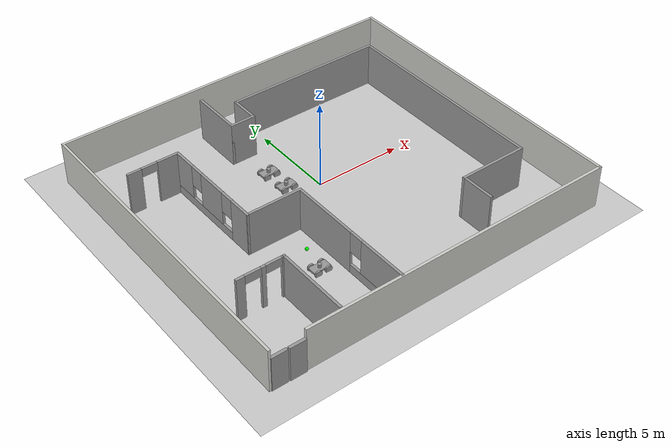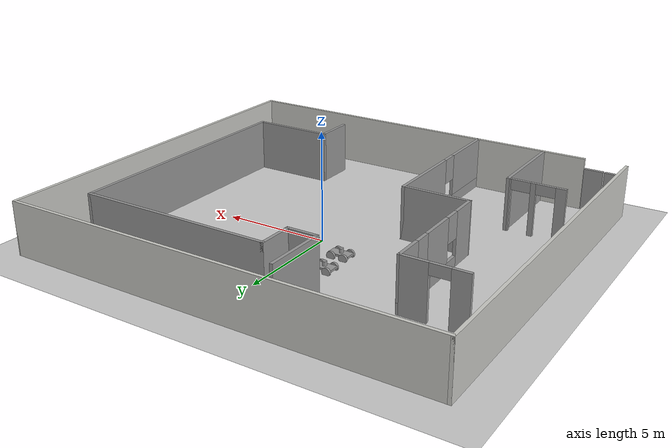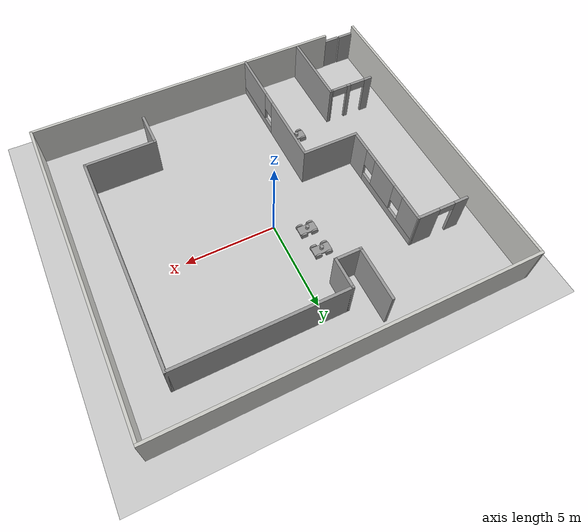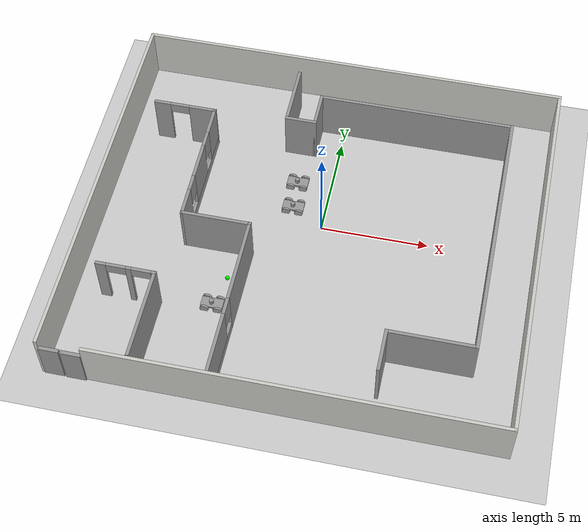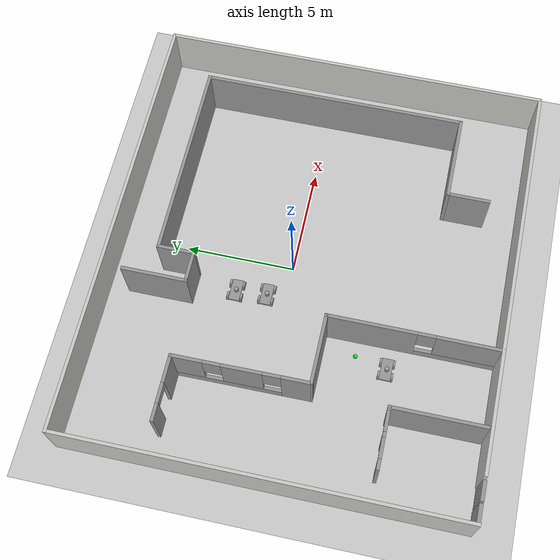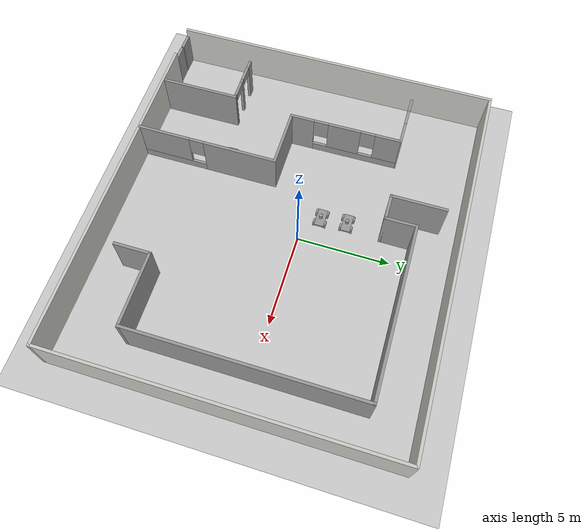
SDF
<sdf version="1.7">
 <world name="__default__">
  <plugin name="hello" filename="libhello.so"/>
  <gravity>0 0 -9.8</gravity>
  <magnetic_field>6e-06 2.3e-05 -4.2e-05</magnetic_field>
  <atmosphere type="adiabatic"/>
  <physics type="ode">
   <max_step_size>0.001</max_step_size>
   <real_time_factor>1</real_time_factor>
   <real_time_update_rate>1000</real_time_update_rate>
  </physics>
  <scene><ambient>0.4 0.4 0.4 1</ambient><background>0.7 0.7 0.7 1</background><shadows>1</shadows></scene>
  <spherical_coordinates>
   <surface_model>EARTH_WGS84</surface_model>
   <latitude_deg>0</latitude_deg>
   <longitude_deg>0</longitude_deg>
   <elevation>0</elevation>
   <heading_deg>0</heading_deg>
  </spherical_coordinates>
  <model name="Building">
   <pose>-0.13002 -0.84943 0 0 -0 0</pose>
   <link name="Door_0">
    <collision name="Door_0_Collision">
     <geometry><box><size>0.9 0.17 2</size></box></geometry>
     <pose>0 0 1 0 -0 0</pose>
    </collision>
    <visual name="Door_0_Visual">
     <pose>0 0 1 0 -0 0</pose>
     <geometry><box><size>0.9 0.17 2</size></box></geometry>
     <material>
      <script><uri>file://media/materials/scripts/gazebo.material</uri><name>Gazebo/Grey</name></script>
     </material>
    </visual>
    <pose>-9.55514 -8.95706 0 0 -0 0</pose>
   </link>
   <link name="Door_1">
    <collision name="Door_1_Collision">
     <geometry><box><size>0.9 0.17 2</size></box></geometry>
     <pose>0 0 1 0 -0 0</pose>
    </collision>
    <visual name="Door_1_Visual">
     <pose>0 0 1 0 -0 0</pose>
     <geometry><box><size>0.9 0.17 2</size></box></geometry>
     <material>
      <script><uri>file://media/materials/scripts/gazebo.material</uri><name>Gazebo/Grey</name></script>
     </material>
    </visual>
    <pose>-8.58516 -8.97356 0 0 -0 0</pose>
   </link>
   <link name="Wall_11">
    <collision name="Wall_11_Collision">
     <geometry><box><size>18.25 0.15 2.5</size></box></geometry>
     <pose>0 0 1.25 0 -0 0</pose>
    </collision>
    <visual name="Wall_11_Visual">
     <pose>0 0 1.25 0 -0 0</pose>
     <geometry><box><size>18.25 0.15 2.5</size></box></geometry>
     <material>
      <script><uri>file://media/materials/scripts/gazebo.material</uri><name>Gazebo/CeilingTiled</name></script>
      <ambient>0.360784 0.207843 0.4 1</ambient>
     </material>
     <meta><layer>0</layer></meta>
    </visual>
    <pose>1.00008 -8.92521 0 0 -0 3.14159</pose>
   </link>
   <link name="Wall_15">
    <collision name="Wall_15_Collision">
     <geometry><box><size>18 0.15 2.5</size></box></geometry>
     <pose>0 0 1.25 0 -0 0</pose>
    </collision>
    <visual name="Wall_15_Visual">
     <pose>0 0 1.25 0 -0 0</pose>
     <geometry><box><size>18 0.15 2.5</size></box></geometry>
     <material>
      <script><uri>file://media/materials/scripts/gazebo.material</uri><name>Gazebo/CeilingTiled</name></script>
      <ambient>0.360784 0.207843 0.4 1</ambient>
     </material>
     <meta><layer>0</layer></meta>
    </visual>
    <pose>-10.0501 0.000212 0 0 -0 -1.5708</pose>
   </link>
   <link name="Wall_2">
    <collision name="Wall_2_Collision">
     <geometry><box><size>20.25 0.15 2.5</size></box></geometry>
     <pose>0 0 1.25 0 -0 0</pose>
    </collision>
    <visual name="Wall_2_Visual">
     <pose>0 0 1.25 0 -0 0</pose>
     <geometry><box><size>20.25 0.15 2.5</size></box></geometry>
     <material>
      <script><uri>file://media/materials/scripts/gazebo.material</uri><name>Gazebo/CeilingTiled</name></script>
      <ambient>0.360784 0.207843 0.4 1</ambient>
     </material>
     <meta><layer>0</layer></meta>
    </visual>
    <pose>0 8.925 0 0 -0 -2.1e-05</pose>
   </link>
   <link name="Wall_3">
    <collision name="Wall_3_Collision">
     <geometry><box><size>18 0.15 2.5</size></box></geometry>
     <pose>0 0 1.25 0 -0 0</pose>
    </collision>
    <visual name="Wall_3_Visual">
     <pose>0 0 1.25 0 -0 0</pose>
     <geometry><box><size>18 0.15 2.5</size></box></geometry>
     <material>
      <script><uri>file://media/materials/scripts/gazebo.material</uri><name>Gazebo/CeilingTiled</name></script>
      <ambient>0.360784 0.207843 0.4 1</ambient>
     </material>
     <meta><layer>0</layer></meta>
    </visual>
    <pose>10.0501 -0.000213 0 0 -0 -1.5708</pose>
   </link>
   <static>1</static>
  </model>
  <model name="building2">
   <pose>-0.46436 -1.33709 0 0 -0 0</pose>
   <link name="Wall_1">
    <collision name="Wall_1_Collision">
     <geometry><box><size>3.25 0.15 2.5</size></box></geometry>
     <pose>0 0 1.25 0 -0 0</pose>
    </collision>
    <visual name="Wall_1_Visual">
     <pose>0 0 1.25 0 -0 0</pose>
     <geometry><box><size>3.25 0.15 2.5</size></box></geometry>
     <material>
      <script><uri>file://media/materials/scripts/gazebo.material</uri><name>Gazebo/Grey</name></script>
      <ambient>1 1 1 1</ambient>
     </material>
     <meta><layer>0</layer></meta>
    </visual>
    <pose>-3.91564 -0.782909 0 0 -0 0</pose>
   </link>
   <link name="Wall_10">
    <pose>-6.93769 5.27004 0 0 -0 3.14159</pose>
    <visual name="Wall_10_Visual_0">
     <pose>-0.850707 0 1.25 0 -0 0</pose>
     <geometry><box><size>1.29859 0.15 2.5</size></box></geometry>
     <material>
      <script><uri>file://media/materials/scripts/gazebo.material</uri><name>Gazebo/Grey</name></script>
      <ambient>1 1 1 1</ambient>
     </material>
     <meta><layer>0</layer></meta>
    </visual>
    <collision name="Wall_10_Collision_0">
     <geometry><box><size>1.29859 0.15 2.5</size></box></geometry>
     <pose>-0.850707 0 1.25 0 -0 0</pose>
    </collision>
    <visual name="Wall_10_Visual_1">
     <pose>1.09929 0 1.25 0 -0 0</pose>
     <geometry><box><size>0.801414 0.15 2.5</size></box></geometry>
     <material>
      <script><uri>file://media/materials/scripts/gazebo.material</uri><name>Gazebo/Grey</name></script>
      <ambient>1 1 1 1</ambient>
     </material>
     <meta><layer>0</layer></meta>
    </visual>
    <collision name="Wall_10_Collision_1">
     <geometry><box><size>0.801414 0.15 2.5</size></box></geometry>
     <pose>1.09929 0 1.25 0 -0 0</pose>
    </collision>
    <visual name="Wall_10_Visual_2">
     <pose>0.248586 0 2.25 0 -0 0</pose>
     <geometry><box><size>0.9 0.15 0.5</size></box></geometry>
     <material>
      <script><uri>file://media/materials/scripts/gazebo.material</uri><name>Gazebo/Grey</name></script>
      <ambient>1 1 1 1</ambient>
     </material>
     <meta><layer>0</layer></meta>
    </visual>
    <collision name="Wall_10_Collision_2">
     <geometry><box><size>0.9 0.15 0.5</size></box></geometry>
     <pose>0.248586 0 2.25 0 -0 0</pose>
    </collision>
   </link>
   <link name="Wall_13">
    <collision name="Wall_13_Collision">
     <geometry><box><size>3 0.15 2.5</size></box></geometry>
     <pose>0 0 1.25 0 -0 0</pose>
    </collision>
    <visual name="Wall_13_Visual">
     <pose>0 0 1.25 0 -0 0</pose>
     <geometry><box><size>3 0.15 2.5</size></box></geometry>
     <material>
      <script><uri>file://media/materials/scripts/gazebo.material</uri><name>Gazebo/Grey</name></script>
      <ambient>1 1 1 1</ambient>
     </material>
     <meta><layer>0</layer></meta>
    </visual>
    <pose>-2.07281 6.95791 0 0 -0 -1.5708</pose>
   </link>
   <link name="Wall_14">
    <collision name="Wall_14_Collision">
     <geometry><box><size>1.5 0.15 2.5</size></box></geometry>
     <pose>0 0 1.25 0 -0 0</pose>
    </collision>
    <visual name="Wall_14_Visual">
     <pose>0 0 1.25 0 -0 0</pose>
     <geometry><box><size>1.5 0.15 2.5</size></box></geometry>
     <material>
      <script><uri>file://media/materials/scripts/gazebo.material</uri><name>Gazebo/Grey</name></script>
      <ambient>1 1 1 1</ambient>
     </material>
     <meta><layer>0</layer></meta>
    </visual>
    <pose>-1.39781 5.53291 0 0 -0 0</pose>
   </link>
   <link name="Wall_15">
    <collision name="Wall_15_Collision">
     <geometry><box><size>1.75 0.15 2.5</size></box></geometry>
     <pose>0 0 1.25 0 -0 0</pose>
    </collision>
    <visual name="Wall_15_Visual">
     <pose>0 0 1.25 0 -0 0</pose>
     <geometry><box><size>1.75 0.15 2.5</size></box></geometry>
     <material>
      <script><uri>file://media/materials/scripts/gazebo.material</uri><name>Gazebo/Grey</name></script>
      <ambient>1 1 1 1</ambient>
     </material>
     <meta><layer>0</layer></meta>
    </visual>
    <pose>-0.722812 6.33291 0 0 -0 1.5708</pose>
   </link>
   <link name="Wall_16">
    <collision name="Wall_16_Collision">
     <geometry><box><size>9.25 0.15 2.5</size></box></geometry>
     <pose>0 0 1.25 0 -0 0</pose>
    </collision>
    <visual name="Wall_16_Visual">
     <pose>0 0 1.25 0 -0 0</pose>
     <geometry><box><size>9.25 0.15 2.5</size></box></geometry>
     <material>
      <script><uri>file://media/materials/scripts/gazebo.material</uri><name>Gazebo/Grey</name></script>
      <ambient>1 1 1 1</ambient>
     </material>
     <meta><layer>0</layer></meta>
    </visual>
    <pose>3.82719 7.13291 0 0 -0 0</pose>
   </link>
   <link name="Wall_18">
    <collision name="Wall_18_Collision">
     <geometry><box><size>12.25 0.15 2.5</size></box></geometry>
     <pose>0 0 1.25 0 -0 0</pose>
    </collision>
    <visual name="Wall_18_Visual">
     <pose>0 0 1.25 0 -0 0</pose>
     <geometry><box><size>12.25 0.15 2.5</size></box></geometry>
     <material>
      <script><uri>file://media/materials/scripts/gazebo.material</uri><name>Gazebo/Grey</name></script>
      <ambient>1 1 1 1</ambient>
     </material>
     <meta><layer>0</layer></meta>
    </visual>
    <pose>8.37719 1.08291 0 0 -0 -1.5708</pose>
   </link>
   <link name="Wall_2">
    <pose>-2.36564 -4.58291 0 0 -0 -1.5708</pose>
    <visual name="Wall_2_Visual_0">
     <pose>-1.85139 0 1.25 0 -0 0</pose>
     <geometry><box><size>4.04722 0.15 2.5</size></box></geometry>
     <material>
      <script><uri>file://media/materials/scripts/gazebo.material</uri><name>Gazebo/Grey</name></script>
      <ambient>1 1 1 1</ambient>
     </material>
     <meta><layer>0</layer></meta>
    </visual>
    <collision name="Wall_2_Collision_0">
     <geometry><box><size>4.04722 0.15 2.5</size></box></geometry>
     <pose>-1.85139 0 1.25 0 -0 0</pose>
    </collision>
    <visual name="Wall_2_Visual_1">
     <pose>2.02361 0 0.25 0 -0 0</pose>
     <geometry><box><size>3.70278 0.15 0.5</size></box></geometry>
     <material>
      <script><uri>file://media/materials/scripts/gazebo.material</uri><name>Gazebo/Grey</name></script>
      <ambient>1 1 1 1</ambient>
     </material>
     <meta><layer>0</layer></meta>
    </visual>
    <collision name="Wall_2_Collision_1">
     <geometry><box><size>3.70278 0.15 0.5</size></box></geometry>
     <pose>2.02361 0 0.25 0 -0 0</pose>
    </collision>
    <visual name="Wall_2_Visual_2">
     <pose>2.42361 0 1.5 0 -0 0</pose>
     <geometry><box><size>2.90278 0.15 2</size></box></geometry>
     <material>
      <script><uri>file://media/materials/scripts/gazebo.material</uri><name>Gazebo/Grey</name></script>
      <ambient>1 1 1 1</ambient>
     </material>
     <meta><layer>0</layer></meta>
    </visual>
    <collision name="Wall_2_Collision_2">
     <geometry><box><size>2.90278 0.15 2</size></box></geometry>
     <pose>2.42361 0 1.5 0 -0 0</pose>
    </collision>
    <visual name="Wall_2_Visual_3">
     <pose>0.57222 0 1.9 0 -0 0</pose>
     <geometry><box><size>0.8 0.15 1.2</size></box></geometry>
     <material>
      <script><uri>file://media/materials/scripts/gazebo.material</uri><name>Gazebo/Grey</name></script>
      <ambient>1 1 1 1</ambient>
     </material>
     <meta><layer>0</layer></meta>
    </visual>
    <collision name="Wall_2_Collision_3">
     <geometry><box><size>0.8 0.15 1.2</size></box></geometry>
     <pose>0.57222 0 1.9 0 -0 0</pose>
    </collision>
   </link>
   <link name="Wall_21">
    <collision name="Wall_21_Collision">
     <geometry><box><size>4 0.15 2.5</size></box></geometry>
     <pose>0 0 1.25 0 -0 0</pose>
    </collision>
    <visual name="Wall_21_Visual">
     <pose>0 0 1.25 0 -0 0</pose>
     <geometry><box><size>4 0.15 2.5</size></box></geometry>
     <material>
      <script><uri>file://media/materials/scripts/gazebo.material</uri><name>Gazebo/Grey</name></script>
      <ambient>1 1 1 1</ambient>
     </material>
     <meta><layer>0</layer></meta>
    </visual>
    <pose>6.45219 -4.96709 0 0 -0 3.14159</pose>
   </link>
   <link name="Wall_22">
    <collision name="Wall_22_Collision">
     <geometry><box><size>2 0.15 2.5</size></box></geometry>
     <pose>0 0 1.25 0 -0 0</pose>
    </collision>
    <visual name="Wall_22_Visual">
     <pose>0 0 1.25 0 -0 0</pose>
     <geometry><box><size>2 0.15 2.5</size></box></geometry>
     <material>
      <script><uri>file://media/materials/scripts/gazebo.material</uri><name>Gazebo/Grey</name></script>
      <ambient>1 1 1 1</ambient>
     </material>
     <meta><layer>0</layer></meta>
    </visual>
    <pose>4.52719 -5.89209 0 0 -0 -1.5708</pose>
   </link>
   <link name="Wall_5">
    <collision name="Wall_5_Collision">
     <geometry><box><size>4.25 0.15 2.5</size></box></geometry>
     <pose>0 0 1.25 0 -0 0</pose>
    </collision>
    <visual name="Wall_5_Visual">
     <pose>0 0 1.25 0 -0 0</pose>
     <geometry><box><size>4.25 0.15 2.5</size></box></geometry>
     <material>
      <script><uri>file://media/materials/scripts/gazebo.material</uri><name>Gazebo/Grey</name></script>
      <ambient>1 1 1 1</ambient>
     </material>
     <meta><layer>0</layer></meta>
    </visual>
    <pose>-5.77719 -6.20253 0 0 -0 -1.5708</pose>
   </link>
   <link name="Wall_7">
    <pose>-7.07719 -4.15253 0 0 -0 3.14159</pose>
    <visual name="Wall_7_Visual_0">
     <pose>-1.25987 0 1.25 0 -0 0</pose>
     <geometry><box><size>0.230254 0.15 2.5</size></box></geometry>
     <material>
      <script><uri>file://media/materials/scripts/gazebo.material</uri><name>Gazebo/Grey</name></script>
      <ambient>1 1 1 1</ambient>
     </material>
     <meta><layer>0</layer></meta>
    </visual>
    <collision name="Wall_7_Collision_0">
     <geometry><box><size>0.230254 0.15 2.5</size></box></geometry>
     <pose>-1.25987 0 1.25 0 -0 0</pose>
    </collision>
    <visual name="Wall_7_Visual_1">
     <pose>-0.1243 0 1.25 0 -0 0</pose>
     <geometry><box><size>0.240891 0.15 2.5</size></box></geometry>
     <material>
      <script><uri>file://media/materials/scripts/gazebo.material</uri><name>Gazebo/Grey</name></script>
      <ambient>1 1 1 1</ambient>
     </material>
     <meta><layer>0</layer></meta>
    </visual>
    <collision name="Wall_7_Collision_1">
     <geometry><box><size>0.240891 0.15 2.5</size></box></geometry>
     <pose>-0.1243 0 1.25 0 -0 0</pose>
    </collision>
    <visual name="Wall_7_Visual_2">
     <pose>1.13557 0 1.25 0 -0 0</pose>
     <geometry><box><size>0.478854 0.15 2.5</size></box></geometry>
     <material>
      <script><uri>file://media/materials/scripts/gazebo.material</uri><name>Gazebo/Grey</name></script>
      <ambient>1 1 1 1</ambient>
     </material>
     <meta><layer>0</layer></meta>
    </visual>
    <collision name="Wall_7_Collision_2">
     <geometry><box><size>0.478854 0.15 2.5</size></box></geometry>
     <pose>1.13557 0 1.25 0 -0 0</pose>
    </collision>
    <visual name="Wall_7_Visual_3">
     <pose>-0.694746 0 2.25 0 -0 0</pose>
     <geometry><box><size>0.9 0.15 0.5</size></box></geometry>
     <material>
      <script><uri>file://media/materials/scripts/gazebo.material</uri><name>Gazebo/Grey</name></script>
      <ambient>1 1 1 1</ambient>
     </material>
     <meta><layer>0</layer></meta>
    </visual>
    <collision name="Wall_7_Collision_3">
     <geometry><box><size>0.9 0.15 0.5</size></box></geometry>
     <pose>-0.694746 0 2.25 0 -0 0</pose>
    </collision>
    <visual name="Wall_7_Visual_4">
     <pose>0.446146 0 2.25 0 -0 0</pose>
     <geometry><box><size>0.9 0.15 0.5</size></box></geometry>
     <material>
      <script><uri>file://media/materials/scripts/gazebo.material</uri><name>Gazebo/Grey</name></script>
      <ambient>1 1 1 1</ambient>
     </material>
     <meta><layer>0</layer></meta>
    </visual>
    <collision name="Wall_7_Collision_4">
     <geometry><box><size>0.9 0.15 0.5</size></box></geometry>
     <pose>0.446146 0 2.25 0 -0 0</pose>
    </collision>
   </link>
   <link name="Wall_9">
    <pose>-5.48916 2.24356 0 0 -0 1.57857</pose>
    <visual name="Wall_9_Visual_0">
     <pose>-2.41932 0 1.25 0 -0 0</pose>
     <geometry><box><size>1.36504 0.15 2.5</size></box></geometry>
     <material>
      <script><uri>file://media/materials/scripts/gazebo.material</uri><name>Gazebo/Grey</name></script>
      <ambient>1 1 1 1</ambient>
     </material>
     <meta><layer>0</layer></meta>
    </visual>
    <collision name="Wall_9_Collision_0">
     <geometry><box><size>1.36504 0.15 2.5</size></box></geometry>
     <pose>-2.41932 0 1.25 0 -0 0</pose>
    </collision>
    <visual name="Wall_9_Visual_1">
     <pose>0.682521 0 0.25 0 -0 0</pose>
     <geometry><box><size>4.83864 0.15 0.5</size></box></geometry>
     <material>
      <script><uri>file://media/materials/scripts/gazebo.material</uri><name>Gazebo/Grey</name></script>
      <ambient>1 1 1 1</ambient>
     </material>
     <meta><layer>0</layer></meta>
    </visual>
    <collision name="Wall_9_Collision_1">
     <geometry><box><size>4.83864 0.15 0.5</size></box></geometry>
     <pose>0.682521 0 0.25 0 -0 0</pose>
    </collision>
    <visual name="Wall_9_Visual_2">
     <pose>-0.039376 0 1.5 0 -0 0</pose>
     <geometry><box><size>1.79484 0.15 2</size></box></geometry>
     <material>
      <script><uri>file://media/materials/scripts/gazebo.material</uri><name>Gazebo/Grey</name></script>
      <ambient>1 1 1 1</ambient>
     </material>
     <meta><layer>0</layer></meta>
    </visual>
    <collision name="Wall_9_Collision_2">
     <geometry><box><size>1.79484 0.15 2</size></box></geometry>
     <pose>-0.039376 0 1.5 0 -0 0</pose>
    </collision>
    <visual name="Wall_9_Visual_3">
     <pose>2.37994 0 1.5 0 -0 0</pose>
     <geometry><box><size>1.44379 0.15 2</size></box></geometry>
     <material>
      <script><uri>file://media/materials/scripts/gazebo.material</uri><name>Gazebo/Grey</name></script>
      <ambient>1 1 1 1</ambient>
     </material>
     <meta><layer>0</layer></meta>
    </visual>
    <collision name="Wall_9_Collision_3">
     <geometry><box><size>1.44379 0.15 2</size></box></geometry>
     <pose>2.37994 0 1.5 0 -0 0</pose>
    </collision>
    <visual name="Wall_9_Visual_4">
     <pose>-1.3368 0 1.9 0 -0 0</pose>
     <geometry><box><size>0.8 0.15 1.2</size></box></geometry>
     <material>
      <script><uri>file://media/materials/scripts/gazebo.material</uri><name>Gazebo/Grey</name></script>
      <ambient>1 1 1 1</ambient>
     </material>
     <meta><layer>0</layer></meta>
    </visual>
    <collision name="Wall_9_Collision_4">
     <geometry><box><size>0.8 0.15 1.2</size></box></geometry>
     <pose>-1.3368 0 1.9 0 -0 0</pose>
    </collision>
    <visual name="Wall_9_Visual_5">
     <pose>1.25805 0 1.9 0 -0 0</pose>
     <geometry><box><size>0.8 0.15 1.2</size></box></geometry>
     <material>
      <script><uri>file://media/materials/scripts/gazebo.material</uri><name>Gazebo/Grey</name></script>
      <ambient>1 1 1 1</ambient>
     </material>
     <meta><layer>0</layer></meta>
    </visual>
    <collision name="Wall_9_Collision_5">
     <geometry><box><size>0.8 0.15 1.2</size></box></geometry>
     <pose>1.25805 0 1.9 0 -0 0</pose>
    </collision>
   </link>
   <static>1</static>
  </model>
  <model name="simplecar">
   <link name="link_0">
    <inertial>
     <mass>1</mass>
     <inertia>
      <ixx>0.166667</ixx>
      <ixy>0</ixy>
      <ixz>0</ixz>
      <iyy>0.166667</iyy>
      <iyz>0</iyz>
      <izz>0.166667</izz>
     </inertia>
    </inertial>
    <pose>0.003333 0.003333 0.147691 0 -0 0</pose>
    <visual name="visual">
     <geometry><box><size>1 0.5 0.1</size></box></geometry>
     <material>
      <lighting>1</lighting>
      <script><uri>file://media/materials/scripts/gazebo.material</uri><name>Gazebo/Grey</name></script>
      <shader type="pixel"><normal_map>__default__</normal_map></shader>
      <ambient>0.3 0.3 0.3 1</ambient>
      <diffuse>0.7 0.7 0.7 1</diffuse>
      <specular>0.01 0.01 0.01 1</specular>
      <emissive>0 0 0 1</emissive>
     </material>
    </visual>
    <collision name="collision">
     <geometry><box><size>1 0.5 0.1</size></box></geometry>
     <surface>
      <friction>
       <ode><mu>1</mu><mu2>1</mu2><fdir1>0 0 0</fdir1><slip1>0</slip1><slip2>0</slip2></ode>
       <torsional>
        <coefficient>1</coefficient>
        <patch_radius>0</patch_radius>
        <surface_radius>0</surface_radius>
        <use_patch_radius>1</use_patch_radius>
        <ode><slip>0</slip></ode>
       </torsional>
      </friction>
      <bounce><restitution_coefficient>0</restitution_coefficient><threshold>1e+06</threshold></bounce>
      <contact>
       <collide_without_contact>0</collide_without_contact>
       <collide_without_contact_bitmask>1</collide_without_contact_bitmask>
       <collide_bitmask>1</collide_bitmask>
       <ode>
        <soft_cfm>0</soft_cfm>
        <soft_erp>0.2</soft_erp>
        <kp>1e+13</kp>
        <kd>1</kd>
        <max_vel>0.01</max_vel>
        <min_depth>0</min_depth>
       </ode>
       <bullet>
        <split_impulse>1</split_impulse>
        <split_impulse_penetration_threshold>-0.01</split_impulse_penetration_threshold>
        <soft_cfm>0</soft_cfm>
        <soft_erp>0.2</soft_erp>
        <kp>1e+13</kp>
        <kd>1</kd>
       </bullet>
      </contact>
     </surface>
    </collision>
   </link>
   <link name="link_1">
    <inertial>
     <mass>1</mass>
     <inertia><ixx>0.145833</ixx><ixy>0</ixy><ixz>0</ixz><iyy>0.145833</iyy><iyz>0</iyz><izz>0.125</izz></inertia>
    </inertial>
    <pose>-0.296667 0.303353 -0.112314 0 -0 0</pose>
    <visual name="visual">
     <pose>0 0 0.2 1.5707 -0 0</pose>
     <geometry><cylinder><radius>0.2</radius><length>0.1</length></cylinder></geometry>
     <material>
      <lighting>1</lighting>
      <script><uri>file://media/materials/scripts/gazebo.material</uri><name>Gazebo/Grey</name></script>
      <shader type="pixel"><normal_map>__default__</normal_map></shader>
      <ambient>0.3 0.3 0.3 1</ambient>
      <diffuse>0.7 0.7 0.7 1</diffuse>
      <specular>0.01 0.01 0.01 1</specular>
      <emissive>0 0 0 1</emissive>
     </material>
    </visual>
    <collision name="collision">
     <pose>0 0 0.2 1.5707 -0 0</pose>
     <geometry><cylinder><radius>0.2</radius><length>0.1</length></cylinder></geometry>
     <surface>
      <friction>
       <ode><mu>1</mu><mu2>1</mu2><fdir1>0 0 0</fdir1><slip1>0</slip1><slip2>0</slip2></ode>
       <torsional>
        <coefficient>1</coefficient>
        <patch_radius>0</patch_radius>
        <surface_radius>0</surface_radius>
        <use_patch_radius>1</use_patch_radius>
        <ode><slip>0</slip></ode>
       </torsional>
      </friction>
      <bounce><restitution_coefficient>0</restitution_coefficient><threshold>1e+06</threshold></bounce>
      <contact>
       <collide_without_contact>0</collide_without_contact>
       <collide_without_contact_bitmask>1</collide_without_contact_bitmask>
       <collide_bitmask>1</collide_bitmask>
       <ode>
        <soft_cfm>0</soft_cfm>
        <soft_erp>0.2</soft_erp>
        <kp>1e+13</kp>
        <kd>1</kd>
        <max_vel>0.01</max_vel>
        <min_depth>0</min_depth>
       </ode>
       <bullet>
        <split_impulse>1</split_impulse>
        <split_impulse_penetration_threshold>-0.01</split_impulse_penetration_threshold>
        <soft_cfm>0</soft_cfm>
        <soft_erp>0.2</soft_erp>
        <kp>1e+13</kp>
        <kd>1</kd>
       </bullet>
      </contact>
     </surface>
    </collision>
   </link>
   <link name="link_1_clone_0">
    <inertial>
     <mass>1</mass>
     <inertia><ixx>0.145833</ixx><ixy>0</ixy><ixz>0</ixz><iyy>0.145833</iyy><iyz>0</iyz><izz>0.125</izz></inertia>
    </inertial>
    <pose>0.303333 0.303353 -0.112314 0 -0 0</pose>
    <visual name="visual">
     <pose>0 0 0.2 1.5707 -0 0</pose>
     <geometry><cylinder><radius>0.2</radius><length>0.1</length></cylinder></geometry>
     <material>
      <lighting>1</lighting>
      <script><uri>file://media/materials/scripts/gazebo.material</uri><name>Gazebo/Grey</name></script>
      <shader type="pixel"><normal_map>__default__</normal_map></shader>
      <ambient>0.3 0.3 0.3 1</ambient>
      <diffuse>0.7 0.7 0.7 1</diffuse>
      <specular>0.01 0.01 0.01 1</specular>
      <emissive>0 0 0 1</emissive>
     </material>
    </visual>
    <collision name="collision">
     <pose>0 0 0.2 1.5707 -0 0</pose>
     <geometry><cylinder><radius>0.2</radius><length>0.1</length></cylinder></geometry>
     <surface>
      <friction>
       <ode><mu>1</mu><mu2>1</mu2><fdir1>0 0 0</fdir1><slip1>0</slip1><slip2>0</slip2></ode>
       <torsional>
        <coefficient>1</coefficient>
        <patch_radius>0</patch_radius>
        <surface_radius>0</surface_radius>
        <use_patch_radius>1</use_patch_radius>
        <ode><slip>0</slip></ode>
       </torsional>
      </friction>
      <bounce><restitution_coefficient>0</restitution_coefficient><threshold>1e+06</threshold></bounce>
      <contact>
       <collide_without_contact>0</collide_without_contact>
       <collide_without_contact_bitmask>1</collide_without_contact_bitmask>
       <collide_bitmask>1</collide_bitmask>
       <ode>
        <soft_cfm>0</soft_cfm>
        <soft_erp>0.2</soft_erp>
        <kp>1e+13</kp>
        <kd>1</kd>
        <max_vel>0.01</max_vel>
        <min_depth>0</min_depth>
       </ode>
       <bullet>
        <split_impulse>1</split_impulse>
        <split_impulse_penetration_threshold>-0.01</split_impulse_penetration_threshold>
        <soft_cfm>0</soft_cfm>
        <soft_erp>0.2</soft_erp>
        <kp>1e+13</kp>
        <kd>1</kd>
       </bullet>
      </contact>
     </surface>
    </collision>
   </link>
   <link name="link_1_clone_1">
    <inertial>
     <mass>1</mass>
     <inertia><ixx>0.145833</ixx><ixy>0</ixy><ixz>0</ixz><iyy>0.145833</iyy><iyz>0</iyz><izz>0.125</izz></inertia>
    </inertial>
    <pose>0.303333 -0.296686 -0.112314 0 -0 0</pose>
    <visual name="visual">
     <pose>0 0 0.2 1.5707 -0 0</pose>
     <geometry><cylinder><radius>0.2</radius><length>0.1</length></cylinder></geometry>
     <material>
      <lighting>1</lighting>
      <script><uri>file://media/materials/scripts/gazebo.material</uri><name>Gazebo/Grey</name></script>
      <shader type="pixel"><normal_map>__default__</normal_map></shader>
      <ambient>0.3 0.3 0.3 1</ambient>
      <diffuse>0.7 0.7 0.7 1</diffuse>
      <specular>0.01 0.01 0.01 1</specular>
      <emissive>0 0 0 1</emissive>
     </material>
    </visual>
    <collision name="collision">
     <pose>0 0 0.2 1.5707 -0 0</pose>
     <geometry><cylinder><radius>0.2</radius><length>0.1</length></cylinder></geometry>
     <surface>
      <friction>
       <ode><mu>1</mu><mu2>1</mu2><fdir1>0 0 0</fdir1><slip1>0</slip1><slip2>0</slip2></ode>
       <torsional>
        <coefficient>1</coefficient>
        <patch_radius>0</patch_radius>
        <surface_radius>0</surface_radius>
        <use_patch_radius>1</use_patch_radius>
        <ode><slip>0</slip></ode>
       </torsional>
      </friction>
      <bounce><restitution_coefficient>0</restitution_coefficient><threshold>1e+06</threshold></bounce>
      <contact>
       <collide_without_contact>0</collide_without_contact>
       <collide_without_contact_bitmask>1</collide_without_contact_bitmask>
       <collide_bitmask>1</collide_bitmask>
       <ode>
        <soft_cfm>0</soft_cfm>
        <soft_erp>0.2</soft_erp>
        <kp>1e+13</kp>
        <kd>1</kd>
        <max_vel>0.01</max_vel>
        <min_depth>0</min_depth>
       </ode>
       <bullet>
        <split_impulse>1</split_impulse>
        <split_impulse_penetration_threshold>-0.01</split_impulse_penetration_threshold>
        <soft_cfm>0</soft_cfm>
        <soft_erp>0.2</soft_erp>
        <kp>1e+13</kp>
        <kd>1</kd>
       </bullet>
      </contact>
     </surface>
    </collision>
   </link>
   <link name="link_1_clone_1_clone">
    <inertial>
     <mass>1</mass>
     <inertia><ixx>0.145833</ixx><ixy>0</ixy><ixz>0</ixz><iyy>0.145833</iyy><iyz>0</iyz><izz>0.125</izz></inertia>
    </inertial>
    <pose>-0.296667 -0.296686 -0.112314 0 -0 0</pose>
    <visual name="visual">
     <pose>0 0 0.2 1.5707 -0 0</pose>
     <geometry><cylinder><radius>0.2</radius><length>0.1</length></cylinder></geometry>
     <material>
      <lighting>1</lighting>
      <script><uri>file://media/materials/scripts/gazebo.material</uri><name>Gazebo/Grey</name></script>
      <shader type="pixel"><normal_map>__default__</normal_map></shader>
      <ambient>0.3 0.3 0.3 1</ambient>
      <diffuse>0.7 0.7 0.7 1</diffuse>
      <specular>0.01 0.01 0.01 1</specular>
      <emissive>0 0 0 1</emissive>
     </material>
    </visual>
    <collision name="collision">
     <pose>0 0 0.2 1.5707 -0 0</pose>
     <geometry><cylinder><radius>0.2</radius><length>0.1</length></cylinder></geometry>
     <surface>
      <friction>
       <ode><mu>1</mu><mu2>1</mu2><fdir1>0 0 0</fdir1><slip1>0</slip1><slip2>0</slip2></ode>
       <torsional>
        <coefficient>1</coefficient>
        <patch_radius>0</patch_radius>
        <surface_radius>0</surface_radius>
        <use_patch_radius>1</use_patch_radius>
        <ode><slip>0</slip></ode>
       </torsional>
      </friction>
      <bounce><restitution_coefficient>0</restitution_coefficient><threshold>1e+06</threshold></bounce>
      <contact>
       <collide_without_contact>0</collide_without_contact>
       <collide_without_contact_bitmask>1</collide_without_contact_bitmask>
       <collide_bitmask>1</collide_bitmask>
       <ode>
        <soft_cfm>0</soft_cfm>
        <soft_erp>0.2</soft_erp>
        <kp>1e+13</kp>
        <kd>1</kd>
        <max_vel>0.01</max_vel>
        <min_depth>0</min_depth>
       </ode>
       <bullet>
        <split_impulse>1</split_impulse>
        <split_impulse_penetration_threshold>-0.01</split_impulse_penetration_threshold>
        <soft_cfm>0</soft_cfm>
        <soft_erp>0.2</soft_erp>
        <kp>1e+13</kp>
        <kd>1</kd>
       </bullet>
      </contact>
     </surface>
    </collision>
   </link>
   <link name="link_3">
    <inertial>
     <mass>1</mass>
     <inertia><ixx>0.145833</ixx><ixy>0</ixy><ixz>0</ixz><iyy>0.145833</iyy><iyz>0</iyz><izz>0.125</izz></inertia>
    </inertial>
    <pose>-0.016667 -0.016667 0.301567 0 -0 0</pose>
    <visual name="visual">
     <geometry><cylinder><radius>0.1</radius><length>0.2</length></cylinder></geometry>
     <material>
      <lighting>1</lighting>
      <script><uri>file://media/materials/scripts/gazebo.material</uri><name>Gazebo/Grey</name></script>
      <shader type="pixel"><normal_map>__default__</normal_map></shader>
      <ambient>0.3 0.3 0.3 1</ambient>
      <diffuse>0.7 0.7 0.7 1</diffuse>
      <specular>0.01 0.01 0.01 1</specular>
      <emissive>0 0 0 1</emissive>
     </material>
    </visual>
    <collision name="collision">
     <geometry><cylinder><radius>0.1</radius><length>0.2</length></cylinder></geometry>
     <surface>
      <friction>
       <ode><mu>1</mu><mu2>1</mu2><fdir1>0 0 0</fdir1><slip1>0</slip1><slip2>0</slip2></ode>
       <torsional>
        <coefficient>1</coefficient>
        <patch_radius>0</patch_radius>
        <surface_radius>0</surface_radius>
        <use_patch_radius>1</use_patch_radius>
        <ode><slip>0</slip></ode>
       </torsional>
      </friction>
      <bounce><restitution_coefficient>0</restitution_coefficient><threshold>1e+06</threshold></bounce>
      <contact>
       <collide_without_contact>0</collide_without_contact>
       <collide_without_contact_bitmask>1</collide_without_contact_bitmask>
       <collide_bitmask>1</collide_bitmask>
       <ode>
        <soft_cfm>0</soft_cfm>
        <soft_erp>0.2</soft_erp>
        <kp>1e+13</kp>
        <kd>1</kd>
        <max_vel>0.01</max_vel>
        <min_depth>0</min_depth>
       </ode>
       <bullet>
        <split_impulse>1</split_impulse>
        <split_impulse_penetration_threshold>-0.01</split_impulse_penetration_threshold>
        <soft_cfm>0</soft_cfm>
        <soft_erp>0.2</soft_erp>
        <kp>1e+13</kp>
        <kd>1</kd>
       </bullet>
      </contact>
     </surface>
    </collision>
   </link>
   <joint name="link_0_JOINT_1" type="revolute">
    <parent>link_0</parent>
    <child>link_1</child>
    <axis>
     <xyz>1 0 0</xyz>
     <limit>
      <lower>-1.79769e+308</lower>
      <upper>1.79769e+308</upper>
      <effort>-1</effort>
      <velocity>-1</velocity>
     </limit>
     <dynamics>
      <spring_reference>0</spring_reference>
      <spring_stiffness>0</spring_stiffness>
      <damping>0</damping>
      <friction>0</friction>
     </dynamics>
    </axis>
    <physics>
     <ode><limit><cfm>0</cfm><erp>0.2</erp></limit><suspension><cfm>0</cfm><erp>0.2</erp></suspension></ode>
    </physics>
   </joint>
   <joint name="link_0_JOINT_2" type="revolute">
    <parent>link_0</parent>
    <child>link_1_clone_1_clone</child>
    <axis>
     <xyz>0 0 1</xyz>
     <limit>
      <lower>-1.79769e+308</lower>
      <upper>1.79769e+308</upper>
      <effort>-1</effort>
      <velocity>-1</velocity>
     </limit>
     <dynamics>
      <spring_reference>0</spring_reference>
      <spring_stiffness>0</spring_stiffness>
      <damping>0</damping>
      <friction>0</friction>
     </dynamics>
    </axis>
    <physics>
     <ode><limit><cfm>0</cfm><erp>0.2</erp></limit><suspension><cfm>0</cfm><erp>0.2</erp></suspension></ode>
    </physics>
   </joint>
   <joint name="link_0_JOINT_3" type="revolute">
    <parent>link_0</parent>
    <child>link_1_clone_1</child>
    <axis>
     <xyz>0 0 1</xyz>
     <limit>
      <lower>-1.79769e+308</lower>
      <upper>1.79769e+308</upper>
      <effort>-1</effort>
      <velocity>-1</velocity>
     </limit>
     <dynamics>
      <spring_reference>0</spring_reference>
      <spring_stiffness>0</spring_stiffness>
      <damping>0</damping>
      <friction>0</friction>
     </dynamics>
    </axis>
    <physics>
     <ode><limit><cfm>0</cfm><erp>0.2</erp></limit><suspension><cfm>0</cfm><erp>0.2</erp></suspension></ode>
    </physics>
   </joint>
   <joint name="link_0_JOINT_4" type="revolute">
    <parent>link_0</parent>
    <child>link_1_clone_0</child>
    <axis>
     <xyz>0 0 1</xyz>
     <limit>
      <lower>-1.79769e+308</lower>
      <upper>1.79769e+308</upper>
      <effort>-1</effort>
      <velocity>-1</velocity>
     </limit>
     <dynamics>
      <spring_reference>0</spring_reference>
      <spring_stiffness>0</spring_stiffness>
      <damping>0</damping>
      <friction>0</friction>
     </dynamics>
    </axis>
    <physics>
     <ode><limit><cfm>0</cfm><erp>0.2</erp></limit><suspension><cfm>0</cfm><erp>0.2</erp></suspension></ode>
    </physics>
   </joint>
   <joint name="link_0_JOINT_5" type="fixed">
    <parent>link_0</parent>
    <child>link_3</child>
    <physics>
     <ode><limit><cfm>0</cfm><erp>0.2</erp></limit><suspension><cfm>0</cfm><erp>0.2</erp></suspension></ode>
    </physics>
   </joint>
   <static>1</static>
   <pose>-3.9241 -5.09042 0 0 -0 0</pose>
  </model>
  <model name="simplecar_clone">
   <link name="link_0">
    <inertial>
     <mass>1</mass>
     <inertia>
      <ixx>0.166667</ixx>
      <ixy>0</ixy>
      <ixz>0</ixz>
      <iyy>0.166667</iyy>
      <iyz>0</iyz>
      <izz>0.166667</izz>
     </inertia>
    </inertial>
    <pose>0.003333 0.003333 0.147691 0 -0 0</pose>
    <visual name="visual">
     <geometry><box><size>1 0.5 0.1</size></box></geometry>
     <material>
      <lighting>1</lighting>
      <script><uri>file://media/materials/scripts/gazebo.material</uri><name>Gazebo/Grey</name></script>
      <shader type="pixel"><normal_map>__default__</normal_map></shader>
      <ambient>0.3 0.3 0.3 1</ambient>
      <diffuse>0.7 0.7 0.7 1</diffuse>
      <specular>0.01 0.01 0.01 1</specular>
      <emissive>0 0 0 1</emissive>
     </material>
    </visual>
    <collision name="collision">
     <geometry><box><size>1 0.5 0.1</size></box></geometry>
     <surface>
      <friction>
       <ode><mu>1</mu><mu2>1</mu2><fdir1>0 0 0</fdir1><slip1>0</slip1><slip2>0</slip2></ode>
       <torsional>
        <coefficient>1</coefficient>
        <patch_radius>0</patch_radius>
        <surface_radius>0</surface_radius>
        <use_patch_radius>1</use_patch_radius>
        <ode><slip>0</slip></ode>
       </torsional>
      </friction>
      <bounce><restitution_coefficient>0</restitution_coefficient><threshold>1e+06</threshold></bounce>
      <contact>
       <collide_without_contact>0</collide_without_contact>
       <collide_without_contact_bitmask>1</collide_without_contact_bitmask>
       <collide_bitmask>1</collide_bitmask>
       <ode>
        <soft_cfm>0</soft_cfm>
        <soft_erp>0.2</soft_erp>
        <kp>1e+13</kp>
        <kd>1</kd>
        <max_vel>0.01</max_vel>
        <min_depth>0</min_depth>
       </ode>
       <bullet>
        <split_impulse>1</split_impulse>
        <split_impulse_penetration_threshold>-0.01</split_impulse_penetration_threshold>
        <soft_cfm>0</soft_cfm>
        <soft_erp>0.2</soft_erp>
        <kp>1e+13</kp>
        <kd>1</kd>
       </bullet>
      </contact>
     </surface>
    </collision>
   </link>
   <link name="link_1">
    <inertial>
     <mass>1</mass>
     <inertia><ixx>0.145833</ixx><ixy>0</ixy><ixz>0</ixz><iyy>0.145833</iyy><iyz>0</iyz><izz>0.125</izz></inertia>
    </inertial>
    <pose>-0.296667 0.303353 -0.112314 0 -0 0</pose>
    <visual name="visual">
     <pose>0 0 0.2 1.5707 -0 0</pose>
     <geometry><cylinder><radius>0.2</radius><length>0.1</length></cylinder></geometry>
     <material>
      <lighting>1</lighting>
      <script><uri>file://media/materials/scripts/gazebo.material</uri><name>Gazebo/Grey</name></script>
      <shader type="pixel"><normal_map>__default__</normal_map></shader>
      <ambient>0.3 0.3 0.3 1</ambient>
      <diffuse>0.7 0.7 0.7 1</diffuse>
      <specular>0.01 0.01 0.01 1</specular>
      <emissive>0 0 0 1</emissive>
     </material>
    </visual>
    <collision name="collision">
     <pose>0 0 0.2 1.5707 -0 0</pose>
     <geometry><cylinder><radius>0.2</radius><length>0.1</length></cylinder></geometry>
     <surface>
      <friction>
       <ode><mu>1</mu><mu2>1</mu2><fdir1>0 0 0</fdir1><slip1>0</slip1><slip2>0</slip2></ode>
       <torsional>
        <coefficient>1</coefficient>
        <patch_radius>0</patch_radius>
        <surface_radius>0</surface_radius>
        <use_patch_radius>1</use_patch_radius>
        <ode><slip>0</slip></ode>
       </torsional>
      </friction>
      <bounce><restitution_coefficient>0</restitution_coefficient><threshold>1e+06</threshold></bounce>
      <contact>
       <collide_without_contact>0</collide_without_contact>
       <collide_without_contact_bitmask>1</collide_without_contact_bitmask>
       <collide_bitmask>1</collide_bitmask>
       <ode>
        <soft_cfm>0</soft_cfm>
        <soft_erp>0.2</soft_erp>
        <kp>1e+13</kp>
        <kd>1</kd>
        <max_vel>0.01</max_vel>
        <min_depth>0</min_depth>
       </ode>
       <bullet>
        <split_impulse>1</split_impulse>
        <split_impulse_penetration_threshold>-0.01</split_impulse_penetration_threshold>
        <soft_cfm>0</soft_cfm>
        <soft_erp>0.2</soft_erp>
        <kp>1e+13</kp>
        <kd>1</kd>
       </bullet>
      </contact>
     </surface>
    </collision>
   </link>
   <link name="link_1_clone_0">
    <inertial>
     <mass>1</mass>
     <inertia><ixx>0.145833</ixx><ixy>0</ixy><ixz>0</ixz><iyy>0.145833</iyy><iyz>0</iyz><izz>0.125</izz></inertia>
    </inertial>
    <pose>0.303333 0.303353 -0.112314 0 -0 0</pose>
    <visual name="visual">
     <pose>0 0 0.2 1.5707 -0 0</pose>
     <geometry><cylinder><radius>0.2</radius><length>0.1</length></cylinder></geometry>
     <material>
      <lighting>1</lighting>
      <script><uri>file://media/materials/scripts/gazebo.material</uri><name>Gazebo/Grey</name></script>
      <shader type="pixel"><normal_map>__default__</normal_map></shader>
      <ambient>0.3 0.3 0.3 1</ambient>
      <diffuse>0.7 0.7 0.7 1</diffuse>
      <specular>0.01 0.01 0.01 1</specular>
      <emissive>0 0 0 1</emissive>
     </material>
    </visual>
    <collision name="collision">
     <pose>0 0 0.2 1.5707 -0 0</pose>
     <geometry><cylinder><radius>0.2</radius><length>0.1</length></cylinder></geometry>
     <surface>
      <friction>
       <ode><mu>1</mu><mu2>1</mu2><fdir1>0 0 0</fdir1><slip1>0</slip1><slip2>0</slip2></ode>
       <torsional>
        <coefficient>1</coefficient>
        <patch_radius>0</patch_radius>
        <surface_radius>0</surface_radius>
        <use_patch_radius>1</use_patch_radius>
        <ode><slip>0</slip></ode>
       </torsional>
      </friction>
      <bounce><restitution_coefficient>0</restitution_coefficient><threshold>1e+06</threshold></bounce>
      <contact>
       <collide_without_contact>0</collide_without_contact>
       <collide_without_contact_bitmask>1</collide_without_contact_bitmask>
       <collide_bitmask>1</collide_bitmask>
       <ode>
        <soft_cfm>0</soft_cfm>
        <soft_erp>0.2</soft_erp>
        <kp>1e+13</kp>
        <kd>1</kd>
        <max_vel>0.01</max_vel>
        <min_depth>0</min_depth>
       </ode>
       <bullet>
        <split_impulse>1</split_impulse>
        <split_impulse_penetration_threshold>-0.01</split_impulse_penetration_threshold>
        <soft_cfm>0</soft_cfm>
        <soft_erp>0.2</soft_erp>
        <kp>1e+13</kp>
        <kd>1</kd>
       </bullet>
      </contact>
     </surface>
    </collision>
   </link>
   <link name="link_1_clone_1">
    <inertial>
     <mass>1</mass>
     <inertia><ixx>0.145833</ixx><ixy>0</ixy><ixz>0</ixz><iyy>0.145833</iyy><iyz>0</iyz><izz>0.125</izz></inertia>
    </inertial>
    <pose>0.303333 -0.296686 -0.112314 0 -0 0</pose>
    <visual name="visual">
     <pose>0 0 0.2 1.5707 -0 0</pose>
     <geometry><cylinder><radius>0.2</radius><length>0.1</length></cylinder></geometry>
     <material>
      <lighting>1</lighting>
      <script><uri>file://media/materials/scripts/gazebo.material</uri><name>Gazebo/Grey</name></script>
      <shader type="pixel"><normal_map>__default__</normal_map></shader>
      <ambient>0.3 0.3 0.3 1</ambient>
      <diffuse>0.7 0.7 0.7 1</diffuse>
      <specular>0.01 0.01 0.01 1</specular>
      <emissive>0 0 0 1</emissive>
     </material>
    </visual>
    <collision name="collision">
     <pose>0 0 0.2 1.5707 -0 0</pose>
     <geometry><cylinder><radius>0.2</radius><length>0.1</length></cylinder></geometry>
     <surface>
      <friction>
       <ode><mu>1</mu><mu2>1</mu2><fdir1>0 0 0</fdir1><slip1>0</slip1><slip2>0</slip2></ode>
       <torsional>
        <coefficient>1</coefficient>
        <patch_radius>0</patch_radius>
        <surface_radius>0</surface_radius>
        <use_patch_radius>1</use_patch_radius>
        <ode><slip>0</slip></ode>
       </torsional>
      </friction>
      <bounce><restitution_coefficient>0</restitution_coefficient><threshold>1e+06</threshold></bounce>
      <contact>
       <collide_without_contact>0</collide_without_contact>
       <collide_without_contact_bitmask>1</collide_without_contact_bitmask>
       <collide_bitmask>1</collide_bitmask>
       <ode>
        <soft_cfm>0</soft_cfm>
        <soft_erp>0.2</soft_erp>
        <kp>1e+13</kp>
        <kd>1</kd>
        <max_vel>0.01</max_vel>
        <min_depth>0</min_depth>
       </ode>
       <bullet>
        <split_impulse>1</split_impulse>
        <split_impulse_penetration_threshold>-0.01</split_impulse_penetration_threshold>
        <soft_cfm>0</soft_cfm>
        <soft_erp>0.2</soft_erp>
        <kp>1e+13</kp>
        <kd>1</kd>
       </bullet>
      </contact>
     </surface>
    </collision>
   </link>
   <link name="link_1_clone_1_clone">
    <inertial>
     <mass>1</mass>
     <inertia><ixx>0.145833</ixx><ixy>0</ixy><ixz>0</ixz><iyy>0.145833</iyy><iyz>0</iyz><izz>0.125</izz></inertia>
    </inertial>
    <pose>-0.296667 -0.296686 -0.112314 0 -0 0</pose>
    <visual name="visual">
     <pose>0 0 0.2 1.5707 -0 0</pose>
     <geometry><cylinder><radius>0.2</radius><length>0.1</length></cylinder></geometry>
     <material>
      <lighting>1</lighting>
      <script><uri>file://media/materials/scripts/gazebo.material</uri><name>Gazebo/Grey</name></script>
      <shader type="pixel"><normal_map>__default__</normal_map></shader>
      <ambient>0.3 0.3 0.3 1</ambient>
      <diffuse>0.7 0.7 0.7 1</diffuse>
      <specular>0.01 0.01 0.01 1</specular>
      <emissive>0 0 0 1</emissive>
     </material>
    </visual>
    <collision name="collision">
     <pose>0 0 0.2 1.5707 -0 0</pose>
     <geometry><cylinder><radius>0.2</radius><length>0.1</length></cylinder></geometry>
     <surface>
      <friction>
       <ode><mu>1</mu><mu2>1</mu2><fdir1>0 0 0</fdir1><slip1>0</slip1><slip2>0</slip2></ode>
       <torsional>
        <coefficient>1</coefficient>
        <patch_radius>0</patch_radius>
        <surface_radius>0</surface_radius>
        <use_patch_radius>1</use_patch_radius>
        <ode><slip>0</slip></ode>
       </torsional>
      </friction>
      <bounce><restitution_coefficient>0</restitution_coefficient><threshold>1e+06</threshold></bounce>
      <contact>
       <collide_without_contact>0</collide_without_contact>
       <collide_without_contact_bitmask>1</collide_without_contact_bitmask>
       <collide_bitmask>1</collide_bitmask>
       <ode>
        <soft_cfm>0</soft_cfm>
        <soft_erp>0.2</soft_erp>
        <kp>1e+13</kp>
        <kd>1</kd>
        <max_vel>0.01</max_vel>
        <min_depth>0</min_depth>
       </ode>
       <bullet>
        <split_impulse>1</split_impulse>
        <split_impulse_penetration_threshold>-0.01</split_impulse_penetration_threshold>
        <soft_cfm>0</soft_cfm>
        <soft_erp>0.2</soft_erp>
        <kp>1e+13</kp>
        <kd>1</kd>
       </bullet>
      </contact>
     </surface>
    </collision>
   </link>
   <link name="link_3">
    <inertial>
     <mass>1</mass>
     <inertia><ixx>0.145833</ixx><ixy>0</ixy><ixz>0</ixz><iyy>0.145833</iyy><iyz>0</iyz><izz>0.125</izz></inertia>
    </inertial>
    <pose>-0.016667 -0.016667 0.301567 0 -0 0</pose>
    <visual name="visual">
     <geometry><cylinder><radius>0.1</radius><length>0.2</length></cylinder></geometry>
     <material>
      <lighting>1</lighting>
      <script><uri>file://media/materials/scripts/gazebo.material</uri><name>Gazebo/Grey</name></script>
      <shader type="pixel"><normal_map>__default__</normal_map></shader>
      <ambient>0.3 0.3 0.3 1</ambient>
      <diffuse>0.7 0.7 0.7 1</diffuse>
      <specular>0.01 0.01 0.01 1</specular>
      <emissive>0 0 0 1</emissive>
     </material>
    </visual>
    <collision name="collision">
     <geometry><cylinder><radius>0.1</radius><length>0.2</length></cylinder></geometry>
     <surface>
      <friction>
       <ode><mu>1</mu><mu2>1</mu2><fdir1>0 0 0</fdir1><slip1>0</slip1><slip2>0</slip2></ode>
       <torsional>
        <coefficient>1</coefficient>
        <patch_radius>0</patch_radius>
        <surface_radius>0</surface_radius>
        <use_patch_radius>1</use_patch_radius>
        <ode><slip>0</slip></ode>
       </torsional>
      </friction>
      <bounce><restitution_coefficient>0</restitution_coefficient><threshold>1e+06</threshold></bounce>
      <contact>
       <collide_without_contact>0</collide_without_contact>
       <collide_without_contact_bitmask>1</collide_without_contact_bitmask>
       <collide_bitmask>1</collide_bitmask>
       <ode>
        <soft_cfm>0</soft_cfm>
        <soft_erp>0.2</soft_erp>
        <kp>1e+13</kp>
        <kd>1</kd>
        <max_vel>0.01</max_vel>
        <min_depth>0</min_depth>
       </ode>
       <bullet>
        <split_impulse>1</split_impulse>
        <split_impulse_penetration_threshold>-0.01</split_impulse_penetration_threshold>
        <soft_cfm>0</soft_cfm>
        <soft_erp>0.2</soft_erp>
        <kp>1e+13</kp>
        <kd>1</kd>
       </bullet>
      </contact>
     </surface>
    </collision>
   </link>
   <joint name="link_0_JOINT_1" type="revolute">
    <parent>link_0</parent>
    <child>link_1</child>
    <axis>
     <xyz>1 0 0</xyz>
     <limit>
      <lower>-1.79769e+308</lower>
      <upper>1.79769e+308</upper>
      <effort>-1</effort>
      <velocity>-1</velocity>
     </limit>
     <dynamics>
      <spring_reference>0</spring_reference>
      <spring_stiffness>0</spring_stiffness>
      <damping>0</damping>
      <friction>0</friction>
     </dynamics>
    </axis>
    <physics>
     <ode><limit><cfm>0</cfm><erp>0.2</erp></limit><suspension><cfm>0</cfm><erp>0.2</erp></suspension></ode>
    </physics>
   </joint>
   <joint name="link_0_JOINT_2" type="revolute">
    <parent>link_0</parent>
    <child>link_1_clone_1_clone</child>
    <axis>
     <xyz>0 0 1</xyz>
     <limit>
      <lower>-1.79769e+308</lower>
      <upper>1.79769e+308</upper>
      <effort>-1</effort>
      <velocity>-1</velocity>
     </limit>
     <dynamics>
      <spring_reference>0</spring_reference>
      <spring_stiffness>0</spring_stiffness>
      <damping>0</damping>
      <friction>0</friction>
     </dynamics>
    </axis>
    <physics>
     <ode><limit><cfm>0</cfm><erp>0.2</erp></limit><suspension><cfm>0</cfm><erp>0.2</erp></suspension></ode>
    </physics>
   </joint>
   <joint name="link_0_JOINT_3" type="revolute">
    <parent>link_0</parent>
    <child>link_1_clone_1</child>
    <axis>
     <xyz>0 0 1</xyz>
     <limit>
      <lower>-1.79769e+308</lower>
      <upper>1.79769e+308</upper>
      <effort>-1</effort>
      <velocity>-1</velocity>
     </limit>
     <dynamics>
      <spring_reference>0</spring_reference>
      <spring_stiffness>0</spring_stiffness>
      <damping>0</damping>
      <friction>0</friction>
     </dynamics>
    </axis>
    <physics>
     <ode><limit><cfm>0</cfm><erp>0.2</erp></limit><suspension><cfm>0</cfm><erp>0.2</erp></suspension></ode>
    </physics>
   </joint>
   <joint name="link_0_JOINT_4" type="revolute">
    <parent>link_0</parent>
    <child>link_1_clone_0</child>
    <axis>
     <xyz>0 0 1</xyz>
     <limit>
      <lower>-1.79769e+308</lower>
      <upper>1.79769e+308</upper>
      <effort>-1</effort>
      <velocity>-1</velocity>
     </limit>
     <dynamics>
      <spring_reference>0</spring_reference>
      <spring_stiffness>0</spring_stiffness>
      <damping>0</damping>
      <friction>0</friction>
     </dynamics>
    </axis>
    <physics>
     <ode><limit><cfm>0</cfm><erp>0.2</erp></limit><suspension><cfm>0</cfm><erp>0.2</erp></suspension></ode>
    </physics>
   </joint>
   <joint name="link_0_JOINT_5" type="fixed">
    <parent>link_0</parent>
    <child>link_3</child>
    <physics>
     <ode><limit><cfm>0</cfm><erp>0.2</erp></limit><suspension><cfm>0</cfm><erp>0.2</erp></suspension></ode>
    </physics>
   </joint>
   <static>1</static>
   <pose>-1.61821 2.30713 0 0 -0 0</pose>
  </model>
  <model name="simplecar_clone_0">
   <link name="link_0">
    <inertial>
     <mass>1</mass>
     <inertia>
      <ixx>0.166667</ixx>
      <ixy>0</ixy>
      <ixz>0</ixz>
      <iyy>0.166667</iyy>
      <iyz>0</iyz>
      <izz>0.166667</izz>
     </inertia>
    </inertial>
    <pose>0.003333 0.003333 0.147691 0 -0 0</pose>
    <visual name="visual">
     <geometry><box><size>1 0.5 0.1</size></box></geometry>
     <material>
      <lighting>1</lighting>
      <script><uri>file://media/materials/scripts/gazebo.material</uri><name>Gazebo/Grey</name></script>
      <shader type="pixel"><normal_map>__default__</normal_map></shader>
      <ambient>0.3 0.3 0.3 1</ambient>
      <diffuse>0.7 0.7 0.7 1</diffuse>
      <specular>0.01 0.01 0.01 1</specular>
      <emissive>0 0 0 1</emissive>
     </material>
    </visual>
    <collision name="collision">
     <geometry><box><size>1 0.5 0.1</size></box></geometry>
     <surface>
      <friction>
       <ode><mu>1</mu><mu2>1</mu2><fdir1>0 0 0</fdir1><slip1>0</slip1><slip2>0</slip2></ode>
       <torsional>
        <coefficient>1</coefficient>
        <patch_radius>0</patch_radius>
        <surface_radius>0</surface_radius>
        <use_patch_radius>1</use_patch_radius>
        <ode><slip>0</slip></ode>
       </torsional>
      </friction>
      <bounce><restitution_coefficient>0</restitution_coefficient><threshold>1e+06</threshold></bounce>
      <contact>
       <collide_without_contact>0</collide_without_contact>
       <collide_without_contact_bitmask>1</collide_without_contact_bitmask>
       <collide_bitmask>1</collide_bitmask>
       <ode>
        <soft_cfm>0</soft_cfm>
        <soft_erp>0.2</soft_erp>
        <kp>1e+13</kp>
        <kd>1</kd>
        <max_vel>0.01</max_vel>
        <min_depth>0</min_depth>
       </ode>
       <bullet>
        <split_impulse>1</split_impulse>
        <split_impulse_penetration_threshold>-0.01</split_impulse_penetration_threshold>
        <soft_cfm>0</soft_cfm>
        <soft_erp>0.2</soft_erp>
        <kp>1e+13</kp>
        <kd>1</kd>
       </bullet>
      </contact>
     </surface>
    </collision>
   </link>
   <link name="link_1">
    <inertial>
     <mass>1</mass>
     <inertia><ixx>0.145833</ixx><ixy>0</ixy><ixz>0</ixz><iyy>0.145833</iyy><iyz>0</iyz><izz>0.125</izz></inertia>
    </inertial>
    <pose>-0.296667 0.303353 -0.112314 0 -0 0</pose>
    <visual name="visual">
     <pose>0 0 0.2 1.5707 -0 0</pose>
     <geometry><cylinder><radius>0.2</radius><length>0.1</length></cylinder></geometry>
     <material>
      <lighting>1</lighting>
      <script><uri>file://media/materials/scripts/gazebo.material</uri><name>Gazebo/Grey</name></script>
      <shader type="pixel"><normal_map>__default__</normal_map></shader>
      <ambient>0.3 0.3 0.3 1</ambient>
      <diffuse>0.7 0.7 0.7 1</diffuse>
      <specular>0.01 0.01 0.01 1</specular>
      <emissive>0 0 0 1</emissive>
     </material>
    </visual>
    <collision name="collision">
     <pose>0 0 0.2 1.5707 -0 0</pose>
     <geometry><cylinder><radius>0.2</radius><length>0.1</length></cylinder></geometry>
     <surface>
      <friction>
       <ode><mu>1</mu><mu2>1</mu2><fdir1>0 0 0</fdir1><slip1>0</slip1><slip2>0</slip2></ode>
       <torsional>
        <coefficient>1</coefficient>
        <patch_radius>0</patch_radius>
        <surface_radius>0</surface_radius>
        <use_patch_radius>1</use_patch_radius>
        <ode><slip>0</slip></ode>
       </torsional>
      </friction>
      <bounce><restitution_coefficient>0</restitution_coefficient><threshold>1e+06</threshold></bounce>
      <contact>
       <collide_without_contact>0</collide_without_contact>
       <collide_without_contact_bitmask>1</collide_without_contact_bitmask>
       <collide_bitmask>1</collide_bitmask>
       <ode>
        <soft_cfm>0</soft_cfm>
        <soft_erp>0.2</soft_erp>
        <kp>1e+13</kp>
        <kd>1</kd>
        <max_vel>0.01</max_vel>
        <min_depth>0</min_depth>
       </ode>
       <bullet>
        <split_impulse>1</split_impulse>
        <split_impulse_penetration_threshold>-0.01</split_impulse_penetration_threshold>
        <soft_cfm>0</soft_cfm>
        <soft_erp>0.2</soft_erp>
        <kp>1e+13</kp>
        <kd>1</kd>
       </bullet>
      </contact>
     </surface>
    </collision>
   </link>
   <link name="link_1_clone_0">
    <inertial>
     <mass>1</mass>
     <inertia><ixx>0.145833</ixx><ixy>0</ixy><ixz>0</ixz><iyy>0.145833</iyy><iyz>0</iyz><izz>0.125</izz></inertia>
    </inertial>
    <pose>0.303333 0.303353 -0.112314 0 -0 0</pose>
    <visual name="visual">
     <pose>0 0 0.2 1.5707 -0 0</pose>
     <geometry><cylinder><radius>0.2</radius><length>0.1</length></cylinder></geometry>
     <material>
      <lighting>1</lighting>
      <script><uri>file://media/materials/scripts/gazebo.material</uri><name>Gazebo/Grey</name></script>
      <shader type="pixel"><normal_map>__default__</normal_map></shader>
      <ambient>0.3 0.3 0.3 1</ambient>
      <diffuse>0.7 0.7 0.7 1</diffuse>
      <specular>0.01 0.01 0.01 1</specular>
      <emissive>0 0 0 1</emissive>
     </material>
    </visual>
    <collision name="collision">
     <pose>0 0 0.2 1.5707 -0 0</pose>
     <geometry><cylinder><radius>0.2</radius><length>0.1</length></cylinder></geometry>
     <surface>
      <friction>
       <ode><mu>1</mu><mu2>1</mu2><fdir1>0 0 0</fdir1><slip1>0</slip1><slip2>0</slip2></ode>
       <torsional>
        <coefficient>1</coefficient>
        <patch_radius>0</patch_radius>
        <surface_radius>0</surface_radius>
        <use_patch_radius>1</use_patch_radius>
        <ode><slip>0</slip></ode>
       </torsional>
      </friction>
      <bounce><restitution_coefficient>0</restitution_coefficient><threshold>1e+06</threshold></bounce>
      <contact>
       <collide_without_contact>0</collide_without_contact>
       <collide_without_contact_bitmask>1</collide_without_contact_bitmask>
       <collide_bitmask>1</collide_bitmask>
       <ode>
        <soft_cfm>0</soft_cfm>
        <soft_erp>0.2</soft_erp>
        <kp>1e+13</kp>
        <kd>1</kd>
        <max_vel>0.01</max_vel>
        <min_depth>0</min_depth>
       </ode>
       <bullet>
        <split_impulse>1</split_impulse>
        <split_impulse_penetration_threshold>-0.01</split_impulse_penetration_threshold>
        <soft_cfm>0</soft_cfm>
        <soft_erp>0.2</soft_erp>
        <kp>1e+13</kp>
        <kd>1</kd>
       </bullet>
      </contact>
     </surface>
    </collision>
   </link>
   <link name="link_1_clone_1">
    <inertial>
     <mass>1</mass>
     <inertia><ixx>0.145833</ixx><ixy>0</ixy><ixz>0</ixz><iyy>0.145833</iyy><iyz>0</iyz><izz>0.125</izz></inertia>
    </inertial>
    <pose>0.303333 -0.296686 -0.112314 0 -0 0</pose>
    <visual name="visual">
     <pose>0 0 0.2 1.5707 -0 0</pose>
     <geometry><cylinder><radius>0.2</radius><length>0.1</length></cylinder></geometry>
     <material>
      <lighting>1</lighting>
      <script><uri>file://media/materials/scripts/gazebo.material</uri><name>Gazebo/Grey</name></script>
      <shader type="pixel"><normal_map>__default__</normal_map></shader>
      <ambient>0.3 0.3 0.3 1</ambient>
      <diffuse>0.7 0.7 0.7 1</diffuse>
      <specular>0.01 0.01 0.01 1</specular>
      <emissive>0 0 0 1</emissive>
     </material>
    </visual>
    <collision name="collision">
     <pose>0 0 0.2 1.5707 -0 0</pose>
     <geometry><cylinder><radius>0.2</radius><length>0.1</length></cylinder></geometry>
     <surface>
      <friction>
       <ode><mu>1</mu><mu2>1</mu2><fdir1>0 0 0</fdir1><slip1>0</slip1><slip2>0</slip2></ode>
       <torsional>
        <coefficient>1</coefficient>
        <patch_radius>0</patch_radius>
        <surface_radius>0</surface_radius>
        <use_patch_radius>1</use_patch_radius>
        <ode><slip>0</slip></ode>
       </torsional>
      </friction>
      <bounce><restitution_coefficient>0</restitution_coefficient><threshold>1e+06</threshold></bounce>
      <contact>
       <collide_without_contact>0</collide_without_contact>
       <collide_without_contact_bitmask>1</collide_without_contact_bitmask>
       <collide_bitmask>1</collide_bitmask>
       <ode>
        <soft_cfm>0</soft_cfm>
        <soft_erp>0.2</soft_erp>
        <kp>1e+13</kp>
        <kd>1</kd>
        <max_vel>0.01</max_vel>
        <min_depth>0</min_depth>
       </ode>
       <bullet>
        <split_impulse>1</split_impulse>
        <split_impulse_penetration_threshold>-0.01</split_impulse_penetration_threshold>
        <soft_cfm>0</soft_cfm>
        <soft_erp>0.2</soft_erp>
        <kp>1e+13</kp>
        <kd>1</kd>
       </bullet>
      </contact>
     </surface>
    </collision>
   </link>
   <link name="link_1_clone_1_clone">
    <inertial>
     <mass>1</mass>
     <inertia><ixx>0.145833</ixx><ixy>0</ixy><ixz>0</ixz><iyy>0.145833</iyy><iyz>0</iyz><izz>0.125</izz></inertia>
    </inertial>
    <pose>-0.296667 -0.296686 -0.112314 0 -0 0</pose>
    <visual name="visual">
     <pose>0 0 0.2 1.5707 -0 0</pose>
     <geometry><cylinder><radius>0.2</radius><length>0.1</length></cylinder></geometry>
     <material>
      <lighting>1</lighting>
      <script><uri>file://media/materials/scripts/gazebo.material</uri><name>Gazebo/Grey</name></script>
      <shader type="pixel"><normal_map>__default__</normal_map></shader>
      <ambient>0.3 0.3 0.3 1</ambient>
      <diffuse>0.7 0.7 0.7 1</diffuse>
      <specular>0.01 0.01 0.01 1</specular>
      <emissive>0 0 0 1</emissive>
     </material>
    </visual>
    <collision name="collision">
     <pose>0 0 0.2 1.5707 -0 0</pose>
     <geometry><cylinder><radius>0.2</radius><length>0.1</length></cylinder></geometry>
     <surface>
      <friction>
       <ode><mu>1</mu><mu2>1</mu2><fdir1>0 0 0</fdir1><slip1>0</slip1><slip2>0</slip2></ode>
       <torsional>
        <coefficient>1</coefficient>
        <patch_radius>0</patch_radius>
        <surface_radius>0</surface_radius>
        <use_patch_radius>1</use_patch_radius>
        <ode><slip>0</slip></ode>
       </torsional>
      </friction>
      <bounce><restitution_coefficient>0</restitution_coefficient><threshold>1e+06</threshold></bounce>
      <contact>
       <collide_without_contact>0</collide_without_contact>
       <collide_without_contact_bitmask>1</collide_without_contact_bitmask>
       <collide_bitmask>1</collide_bitmask>
       <ode>
        <soft_cfm>0</soft_cfm>
        <soft_erp>0.2</soft_erp>
        <kp>1e+13</kp>
        <kd>1</kd>
        <max_vel>0.01</max_vel>
        <min_depth>0</min_depth>
       </ode>
       <bullet>
        <split_impulse>1</split_impulse>
        <split_impulse_penetration_threshold>-0.01</split_impulse_penetration_threshold>
        <soft_cfm>0</soft_cfm>
        <soft_erp>0.2</soft_erp>
        <kp>1e+13</kp>
        <kd>1</kd>
       </bullet>
      </contact>
     </surface>
    </collision>
   </link>
   <link name="link_3">
    <inertial>
     <mass>1</mass>
     <inertia><ixx>0.145833</ixx><ixy>0</ixy><ixz>0</ixz><iyy>0.145833</iyy><iyz>0</iyz><izz>0.125</izz></inertia>
    </inertial>
    <pose>-0.016667 -0.016667 0.301567 0 -0 0</pose>
    <visual name="visual">
     <geometry><cylinder><radius>0.1</radius><length>0.2</length></cylinder></geometry>
     <material>
      <lighting>1</lighting>
      <script><uri>file://media/materials/scripts/gazebo.material</uri><name>Gazebo/Grey</name></script>
      <shader type="pixel"><normal_map>__default__</normal_map></shader>
      <ambient>0.3 0.3 0.3 1</ambient>
      <diffuse>0.7 0.7 0.7 1</diffuse>
      <specular>0.01 0.01 0.01 1</specular>
      <emissive>0 0 0 1</emissive>
     </material>
    </visual>
    <collision name="collision">
     <geometry><cylinder><radius>0.1</radius><length>0.2</length></cylinder></geometry>
     <surface>
      <friction>
       <ode><mu>1</mu><mu2>1</mu2><fdir1>0 0 0</fdir1><slip1>0</slip1><slip2>0</slip2></ode>
       <torsional>
        <coefficient>1</coefficient>
        <patch_radius>0</patch_radius>
        <surface_radius>0</surface_radius>
        <use_patch_radius>1</use_patch_radius>
        <ode><slip>0</slip></ode>
       </torsional>
      </friction>
      <bounce><restitution_coefficient>0</restitution_coefficient><threshold>1e+06</threshold></bounce>
      <contact>
       <collide_without_contact>0</collide_without_contact>
       <collide_without_contact_bitmask>1</collide_without_contact_bitmask>
       <collide_bitmask>1</collide_bitmask>
       <ode>
        <soft_cfm>0</soft_cfm>
        <soft_erp>0.2</soft_erp>
        <kp>1e+13</kp>
        <kd>1</kd>
        <max_vel>0.01</max_vel>
        <min_depth>0</min_depth>
       </ode>
       <bullet>
        <split_impulse>1</split_impulse>
        <split_impulse_penetration_threshold>-0.01</split_impulse_penetration_threshold>
        <soft_cfm>0</soft_cfm>
        <soft_erp>0.2</soft_erp>
        <kp>1e+13</kp>
        <kd>1</kd>
       </bullet>
      </contact>
     </surface>
    </collision>
   </link>
   <joint name="link_0_JOINT_1" type="revolute">
    <parent>link_0</parent>
    <child>link_1</child>
    <axis>
     <xyz>1 0 0</xyz>
     <limit>
      <lower>-1.79769e+308</lower>
      <upper>1.79769e+308</upper>
      <effort>-1</effort>
      <velocity>-1</velocity>
     </limit>
     <dynamics>
      <spring_reference>0</spring_reference>
      <spring_stiffness>0</spring_stiffness>
      <damping>0</damping>
      <friction>0</friction>
     </dynamics>
    </axis>
    <physics>
     <ode><limit><cfm>0</cfm><erp>0.2</erp></limit><suspension><cfm>0</cfm><erp>0.2</erp></suspension></ode>
    </physics>
   </joint>
   <joint name="link_0_JOINT_2" type="revolute">
    <parent>link_0</parent>
    <child>link_1_clone_1_clone</child>
    <axis>
     <xyz>0 0 1</xyz>
     <limit>
      <lower>-1.79769e+308</lower>
      <upper>1.79769e+308</upper>
      <effort>-1</effort>
      <velocity>-1</velocity>
     </limit>
     <dynamics>
      <spring_reference>0</spring_reference>
      <spring_stiffness>0</spring_stiffness>
      <damping>0</damping>
      <friction>0</friction>
     </dynamics>
    </axis>
    <physics>
     <ode><limit><cfm>0</cfm><erp>0.2</erp></limit><suspension><cfm>0</cfm><erp>0.2</erp></suspension></ode>
    </physics>
   </joint>
   <joint name="link_0_JOINT_3" type="revolute">
    <parent>link_0</parent>
    <child>link_1_clone_1</child>
    <axis>
     <xyz>0 0 1</xyz>
     <limit>
      <lower>-1.79769e+308</lower>
      <upper>1.79769e+308</upper>
      <effort>-1</effort>
      <velocity>-1</velocity>
     </limit>
     <dynamics>
      <spring_reference>0</spring_reference>
      <spring_stiffness>0</spring_stiffness>
      <damping>0</damping>
      <friction>0</friction>
     </dynamics>
    </axis>
    <physics>
     <ode><limit><cfm>0</cfm><erp>0.2</erp></limit><suspension><cfm>0</cfm><erp>0.2</erp></suspension></ode>
    </physics>
   </joint>
   <joint name="link_0_JOINT_4" type="revolute">
    <parent>link_0</parent>
    <child>link_1_clone_0</child>
    <axis>
     <xyz>0 0 1</xyz>
     <limit>
      <lower>-1.79769e+308</lower>
      <upper>1.79769e+308</upper>
      <effort>-1</effort>
      <velocity>-1</velocity>
     </limit>
     <dynamics>
      <spring_reference>0</spring_reference>
      <spring_stiffness>0</spring_stiffness>
      <damping>0</damping>
      <friction>0</friction>
     </dynamics>
    </axis>
    <physics>
     <ode><limit><cfm>0</cfm><erp>0.2</erp></limit><suspension><cfm>0</cfm><erp>0.2</erp></suspension></ode>
    </physics>
   </joint>
   <joint name="link_0_JOINT_5" type="fixed">
    <parent>link_0</parent>
    <child>link_3</child>
    <physics>
     <ode><limit><cfm>0</cfm><erp>0.2</erp></limit><suspension><cfm>0</cfm><erp>0.2</erp></suspension></ode>
    </physics>
   </joint>
   <static>1</static>
   <pose>-1.52744 0.886682 0 0 -0 0</pose>
  </model>
  <model name="ground_plane">
   <static>1</static>
   <link name="link">
    <collision name="collision">
     <geometry><plane><normal>0 0 1</normal><size>100 100</size></plane></geometry>
     <surface>
      <contact><collide_bitmask>65535</collide_bitmask></contact>
      <friction><ode><mu>100</mu><mu2>50</mu2></ode></friction>
     </surface>
    </collision>
    <visual name="visual">
     <cast_shadows>0</cast_shadows>
     <geometry><plane><normal>0 0 1</normal><size>100 100</size></plane></geometry>
     <material>
      <script><uri>file://media/materials/scripts/gazebo.material</uri><name>Gazebo/Grey</name></script>
     </material>
    </visual>
   </link>
   <pose>-59.0264 48.4098 0 0 -0 0</pose>
  </model>
  <model name="greenball">
   <link name="link_0">
    <inertial>
     <mass>1</mass>
     <inertia><ixx>0.1</ixx><ixy>0</ixy><ixz>0</ixz><iyy>0.1</iyy><iyz>0</iyz><izz>0.1</izz></inertia>
    </inertial>
    <visual name="visual">
     <geometry><sphere><radius>0.1</radius></sphere></geometry>
     <material>
      <lighting>1</lighting>
      <script><uri>file://media/materials/scripts/gazebo.material</uri><name>Gazebo/Grey</name></script>
      <shader type="pixel"><normal_map>__default__</normal_map></shader>
      <ambient>0 1 0 1</ambient>
      <diffuse>0.7 0.7 0.7 1</diffuse>
      <specular>0.01 0.01 0.01 1</specular>
      <emissive>0 0 0 1</emissive>
     </material>
    </visual>
    <collision name="collision">
     <geometry><sphere><radius>0.1</radius></sphere></geometry>
     <surface>
      <friction>
       <ode><mu>1</mu><mu2>1</mu2><fdir1>0 0 0</fdir1><slip1>0</slip1><slip2>0</slip2></ode>
       <torsional>
        <coefficient>1</coefficient>
        <patch_radius>0</patch_radius>
        <surface_radius>0</surface_radius>
        <use_patch_radius>1</use_patch_radius>
        <ode><slip>0</slip></ode>
       </torsional>
      </friction>
      <bounce><restitution_coefficient>0</restitution_coefficient><threshold>1e+06</threshold></bounce>
      <contact>
       <collide_without_contact>0</collide_without_contact>
       <collide_without_contact_bitmask>1</collide_without_contact_bitmask>
       <collide_bitmask>1</collide_bitmask>
       <ode>
        <soft_cfm>0</soft_cfm>
        <soft_erp>0.2</soft_erp>
        <kp>1e+13</kp>
        <kd>1</kd>
        <max_vel>0.01</max_vel>
        <min_depth>0</min_depth>
       </ode>
       <bullet>
        <split_impulse>1</split_impulse>
        <split_impulse_penetration_threshold>-0.01</split_impulse_penetration_threshold>
        <soft_cfm>0</soft_cfm>
        <soft_erp>0.2</soft_erp>
        <kp>1e+13</kp>
        <kd>1</kd>
       </bullet>
      </contact>
     </surface>
    </collision>
   </link>
   <static>0</static>
   <pose>-3.5904 -3.62837 0.1 0 -0 0</pose>
  </model>
 </world>
</sdf>
